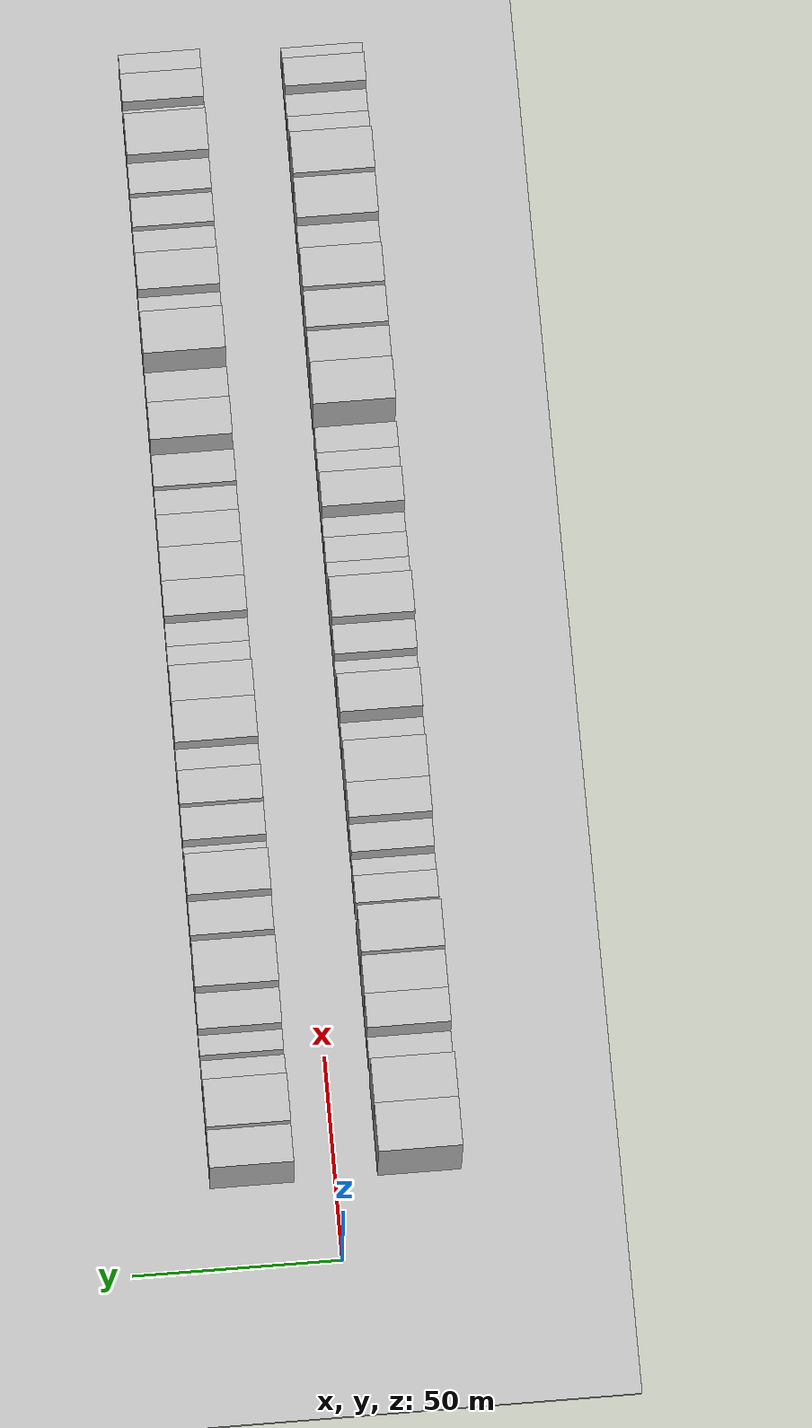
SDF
<?xml version="1.0" encoding="utf-8"?>

<sdf version="1.6">

   <world name="default">

      <gui fullscreen="0">

         <camera name="user_camera">

            <pose>-15 0 4.57585 0 0 0</pose>

            <view_controller>orbit</view_controller>

         </camera>

      </gui>

      <scene>

         <sky>

           <clouds>

             <speed>12</speed>

           </clouds>

         </sky>

         <ambient>0.4 0.4 0.4 1</ambient>

         <background>0.7 0.7 0.7 1</background>

         <shadows>1</shadows>

      </scene>

      <gravity>0 0 -9.8066</gravity>

      <magnetic_field>6e-06 2.3e-05 -4.2e-05</magnetic_field>

      <physics default="0" name="default_physics" type="ode">

         <ode>

            <solver>

               <type>quick</type>

               <iters>10</iters>

               <sor>1.0</sor>

               <use_dynamic_moi_rescaling>0</use_dynamic_moi_rescaling>

            </solver>

            <constraints>

               <cfm>0</cfm>

               <erp>0.2</erp>

               <contact_max_correcting_vel>100</contact_max_correcting_vel>

               <contact_surface_layer>0.001</contact_surface_layer>

            </constraints>

         </ode>

         <max_step_size>0.004</max_step_size>

         <real_time_factor>1</real_time_factor>

         <real_time_update_rate>250</real_time_update_rate>

      </physics>

      <light name="sun" type="directional">

         <cast_shadows>1</cast_shadows>

         <pose>0 0 10 0 0 0</pose>

         <diffuse>0.8 0.8 0.8 1</diffuse>

         <specular>0.2 0.2 0.2 1</specular>

         <attenuation>

            <range>1000</range>

            <constant>0.9</constant>

            <linear>0.01</linear>

            <quadratic>0.001</quadratic>

         </attenuation>

         <direction>-0.5 0.1 -0.9</direction>

      </light>

      <include>

         <name>ground_plane_1</name>

         <uri>model://HANNAS_ground_plane</uri>

         <pose>0 0 0  0 0 0</pose>

      </include>

      <include>

         <name>ground_plane_2</name>

         <uri>model://HANNAS_ground_plane</uri>

         <pose>100 0 0  0 0 0</pose>

      </include>

      <model name="building_1">

         <static>1</static>

         <pose frame="">24.6154 20.0000 0 0.000000 0.000000 1.570796</pose>

         <link name="link">

            <pose frame="">0 0 10.50 0 0 0</pose>

            <collision name="collision">

               <geometry>

                  <box>

                     <size>20.0000 9.2307 21.0000</size>

                  </box>

               </geometry>

               <max_contacts>10</max_contacts>

               <surface>

                  <contact>

                     <ode/>

                  </contact>

                  <bounce/>

                  <friction>

                     <torsional>

                        <ode/>

                     </torsional>

                     <ode/>

                  </friction>

               </surface>

            </collision>

            <visual name="visual">

               <cast_shadows>0</cast_shadows>

               <geometry>

                  <box>

                     <size>20.0000 9.2307 21.0000</size>

                  </box>

               </geometry>

               <material>

                  <script>

                     <uri>model://HANNAS_wall/materials/scripts</uri>

                     <uri>model://HANNAS_wall/materials/textures</uri>

                     <name>vrc/HANNAS_wall</name>

                  </script>

               </material>

            </visual>

            <self_collide>0</self_collide>

            <enable_wind>0</enable_wind>

            <kinematic>0</kinematic>

         </link>

      </model>

      <model name="building_2">

         <static>1</static>

         <pose frame="">35.0574 20.0000 0 0.000000 0.000000 1.570796</pose>

         <link name="link">

            <pose frame="">0 0 12.00 0 0 0</pose>

            <collision name="collision">

               <geometry>

                  <box>

                     <size>20.0000 11.6533 24.0000</size>

                  </box>

               </geometry>

               <max_contacts>10</max_contacts>

               <surface>

                  <contact>

                     <ode/>

                  </contact>

                  <bounce/>

                  <friction>

                     <torsional>

                        <ode/>

                     </torsional>

                     <ode/>

                  </friction>

               </surface>

            </collision>

            <visual name="visual">

               <cast_shadows>0</cast_shadows>

               <geometry>

                  <box>

                     <size>20.0000 11.6533 24.0000</size>

                  </box>

               </geometry>

               <material>

                  <script>

                     <uri>model://HANNAS_wall/materials/scripts</uri>

                     <uri>model://HANNAS_wall/materials/textures</uri>

                     <name>vrc/HANNAS_wall</name>

                  </script>

               </material>

            </visual>

            <self_collide>0</self_collide>

            <enable_wind>0</enable_wind>

            <kinematic>0</kinematic>

         </link>

      </model>

      <model name="building_3">

         <static>1</static>

         <pose frame="">44.3191 20.0000 0 0.000000 0.000000 1.570796</pose>

         <link name="link">

            <pose frame="">0 0 7.50 0 0 0</pose>

            <collision name="collision">

               <geometry>

                  <box>

                     <size>20.0000 6.8702 15.0000</size>

                  </box>

               </geometry>

               <max_contacts>10</max_contacts>

               <surface>

                  <contact>

                     <ode/>

                  </contact>

                  <bounce/>

                  <friction>

                     <torsional>

                        <ode/>

                     </torsional>

                     <ode/>

                  </friction>

               </surface>

            </collision>

            <visual name="visual">

               <cast_shadows>0</cast_shadows>

               <geometry>

                  <box>

                     <size>20.0000 6.8702 15.0000</size>

                  </box>

               </geometry>

               <material>

                  <script>

                     <uri>model://HANNAS_wall/materials/scripts</uri>

                     <uri>model://HANNAS_wall/materials/textures</uri>

                     <name>vrc/HANNAS_wall</name>

                  </script>

               </material>

            </visual>

            <self_collide>0</self_collide>

            <enable_wind>0</enable_wind>

            <kinematic>0</kinematic>

         </link>

      </model>

      <model name="building_4">

         <static>1</static>

         <pose frame="">52.2593 20.0000 0 0.000000 0.000000 1.570796</pose>

         <link name="link">

            <pose frame="">0 0 6.00 0 0 0</pose>

            <collision name="collision">

               <geometry>

                  <box>

                     <size>20.0000 5.0101 12.0000</size>

                  </box>

               </geometry>

               <max_contacts>10</max_contacts>

               <surface>

                  <contact>

                     <ode/>

                  </contact>

                  <bounce/>

                  <friction>

                     <torsional>

                        <ode/>

                     </torsional>

                     <ode/>

                  </friction>

               </surface>

            </collision>

            <visual name="visual">

               <cast_shadows>0</cast_shadows>

               <geometry>

                  <box>

                     <size>20.0000 5.0101 12.0000</size>

                  </box>

               </geometry>

               <material>

                  <script>

                     <uri>model://HANNAS_wall/materials/scripts</uri>

                     <uri>model://HANNAS_wall/materials/textures</uri>

                     <name>vrc/HANNAS_wall</name>

                  </script>

               </material>

            </visual>

            <self_collide>0</self_collide>

            <enable_wind>0</enable_wind>

            <kinematic>0</kinematic>

         </link>

      </model>

      <model name="building_5">

         <static>1</static>

         <pose frame="">59.1592 20.0000 0 0.000000 0.000000 1.570796</pose>

         <link name="link">

            <pose frame="">0 0 9.00 0 0 0</pose>

            <collision name="collision">

               <geometry>

                  <box>

                     <size>20.0000 8.7898 18.0000</size>

                  </box>

               </geometry>

               <max_contacts>10</max_contacts>

               <surface>

                  <contact>

                     <ode/>

                  </contact>

                  <bounce/>

                  <friction>

                     <torsional>

                        <ode/>

                     </torsional>

                     <ode/>

                  </friction>

               </surface>

            </collision>

            <visual name="visual">

               <cast_shadows>0</cast_shadows>

               <geometry>

                  <box>

                     <size>20.0000 8.7898 18.0000</size>

                  </box>

               </geometry>

               <material>

                  <script>

                     <uri>model://HANNAS_wall/materials/scripts</uri>

                     <uri>model://HANNAS_wall/materials/textures</uri>

                     <name>vrc/HANNAS_wall</name>

                  </script>

               </material>

            </visual>

            <self_collide>0</self_collide>

            <enable_wind>0</enable_wind>

            <kinematic>0</kinematic>

         </link>

      </model>

      <model name="building_6">

         <static>1</static>

         <pose frame="">69.2039 20.0000 0 0.000000 0.000000 1.570796</pose>

         <link name="link">

            <pose frame="">0 0 12.00 0 0 0</pose>

            <collision name="collision">

               <geometry>

                  <box>

                     <size>20.0000 11.2996 24.0000</size>

                  </box>

               </geometry>

               <max_contacts>10</max_contacts>

               <surface>

                  <contact>

                     <ode/>

                  </contact>

                  <bounce/>

                  <friction>

                     <torsional>

                        <ode/>

                     </torsional>

                     <ode/>

                  </friction>

               </surface>

            </collision>

            <visual name="visual">

               <cast_shadows>0</cast_shadows>

               <geometry>

                  <box>

                     <size>20.0000 11.2996 24.0000</size>

                  </box>

               </geometry>

               <material>

                  <script>

                     <uri>model://HANNAS_wall/materials/scripts</uri>

                     <uri>model://HANNAS_wall/materials/textures</uri>

                     <name>vrc/HANNAS_wall</name>

                  </script>

               </material>

            </visual>

            <self_collide>0</self_collide>

            <enable_wind>0</enable_wind>

            <kinematic>0</kinematic>

         </link>

      </model>

      <model name="building_7">

         <static>1</static>

         <pose frame="">82.0477 20.0000 0 0.000000 0.000000 1.570796</pose>

         <link name="link">

            <pose frame="">0 0 9.00 0 0 0</pose>

            <collision name="collision">

               <geometry>

                  <box>

                     <size>20.0000 8.3880 18.0000</size>

                  </box>

               </geometry>

               <max_contacts>10</max_contacts>

               <surface>

                  <contact>

                     <ode/>

                  </contact>

                  <bounce/>

                  <friction>

                     <torsional>

                        <ode/>

                     </torsional>

                     <ode/>

                  </friction>

               </surface>

            </collision>

            <visual name="visual">

               <cast_shadows>0</cast_shadows>

               <geometry>

                  <box>

                     <size>20.0000 8.3880 18.0000</size>

                  </box>

               </geometry>

               <material>

                  <script>

                     <uri>model://HANNAS_wall/materials/scripts</uri>

                     <uri>model://HANNAS_wall/materials/textures</uri>

                     <name>vrc/HANNAS_wall</name>

                  </script>

               </material>

            </visual>

            <self_collide>0</self_collide>

            <enable_wind>0</enable_wind>

            <kinematic>0</kinematic>

         </link>

      </model>

      <model name="building_8">

         <static>1</static>

         <pose frame="">91.3459 20.0000 0 0.000000 0.000000 1.570796</pose>

         <link name="link">

            <pose frame="">0 0 12.00 0 0 0</pose>

            <collision name="collision">

               <geometry>

                  <box>

                     <size>20.0000 10.2082 24.0000</size>

                  </box>

               </geometry>

               <max_contacts>10</max_contacts>

               <surface>

                  <contact>

                     <ode/>

                  </contact>

                  <bounce/>

                  <friction>

                     <torsional>

                        <ode/>

                     </torsional>

                     <ode/>

                  </friction>

               </surface>

            </collision>

            <visual name="visual">

               <cast_shadows>0</cast_shadows>

               <geometry>

                  <box>

                     <size>20.0000 10.2082 24.0000</size>

                  </box>

               </geometry>

               <material>

                  <script>

                     <uri>model://HANNAS_wall/materials/scripts</uri>

                     <uri>model://HANNAS_wall/materials/textures</uri>

                     <name>vrc/HANNAS_wall</name>

                  </script>

               </material>

            </visual>

            <self_collide>0</self_collide>

            <enable_wind>0</enable_wind>

            <kinematic>0</kinematic>

         </link>

      </model>

      <model name="building_9">

         <static>1</static>

         <pose frame="">98.9628 20.0000 0 0.000000 0.000000 1.570796</pose>

         <link name="link">

            <pose frame="">0 0 6.00 0 0 0</pose>

            <collision name="collision">

               <geometry>

                  <box>

                     <size>20.0000 5.0256 12.0000</size>

                  </box>

               </geometry>

               <max_contacts>10</max_contacts>

               <surface>

                  <contact>

                     <ode/>

                  </contact>

                  <bounce/>

                  <friction>

                     <torsional>

                        <ode/>

                     </torsional>

                     <ode/>

                  </friction>

               </surface>

            </collision>

            <visual name="visual">

               <cast_shadows>0</cast_shadows>

               <geometry>

                  <box>

                     <size>20.0000 5.0256 12.0000</size>

                  </box>

               </geometry>

               <material>

                  <script>

                     <uri>model://HANNAS_wall/materials/scripts</uri>

                     <uri>model://HANNAS_wall/materials/textures</uri>

                     <name>vrc/HANNAS_wall</name>

                  </script>

               </material>

            </visual>

            <self_collide>0</self_collide>

            <enable_wind>0</enable_wind>

            <kinematic>0</kinematic>

         </link>

      </model>

      <model name="building_10">

         <static>1</static>

         <pose frame="">105.5644 20.0000 0 0.000000 0.000000 1.570796</pose>

         <link name="link">

            <pose frame="">0 0 9.00 0 0 0</pose>

            <collision name="collision">

               <geometry>

                  <box>

                     <size>20.0000 8.1775 18.0000</size>

                  </box>

               </geometry>

               <max_contacts>10</max_contacts>

               <surface>

                  <contact>

                     <ode/>

                  </contact>

                  <bounce/>

                  <friction>

                     <torsional>

                        <ode/>

                     </torsional>

                     <ode/>

                  </friction>

               </surface>

            </collision>

            <visual name="visual">

               <cast_shadows>0</cast_shadows>

               <geometry>

                  <box>

                     <size>20.0000 8.1775 18.0000</size>

                  </box>

               </geometry>

               <material>

                  <script>

                     <uri>model://HANNAS_wall/materials/scripts</uri>

                     <uri>model://HANNAS_wall/materials/textures</uri>

                     <name>vrc/HANNAS_wall</name>

                  </script>

               </material>

            </visual>

            <self_collide>0</self_collide>

            <enable_wind>0</enable_wind>

            <kinematic>0</kinematic>

         </link>

      </model>

      <model name="building_11">

         <static>1</static>

         <pose frame="">113.8745 20.0000 0 0.000000 0.000000 1.570796</pose>

         <link name="link">

            <pose frame="">0 0 10.50 0 0 0</pose>

            <collision name="collision">

               <geometry>

                  <box>

                     <size>20.0000 8.4427 21.0000</size>

                  </box>

               </geometry>

               <max_contacts>10</max_contacts>

               <surface>

                  <contact>

                     <ode/>

                  </contact>

                  <bounce/>

                  <friction>

                     <torsional>

                        <ode/>

                     </torsional>

                     <ode/>

                  </friction>

               </surface>

            </collision>

            <visual name="visual">

               <cast_shadows>0</cast_shadows>

               <geometry>

                  <box>

                     <size>20.0000 8.4427 21.0000</size>

                  </box>

               </geometry>

               <material>

                  <script>

                     <uri>model://HANNAS_wall/materials/scripts</uri>

                     <uri>model://HANNAS_wall/materials/textures</uri>

                     <name>vrc/HANNAS_wall</name>

                  </script>

               </material>

            </visual>

            <self_collide>0</self_collide>

            <enable_wind>0</enable_wind>

            <kinematic>0</kinematic>

         </link>

      </model>

      <model name="building_12">

         <static>1</static>

         <pose frame="">121.5920 20.0000 0 0.000000 0.000000 1.570796</pose>

         <link name="link">

            <pose frame="">0 0 7.50 0 0 0</pose>

            <collision name="collision">

               <geometry>

                  <box>

                     <size>20.0000 6.9923 15.0000</size>

                  </box>

               </geometry>

               <max_contacts>10</max_contacts>

               <surface>

                  <contact>

                     <ode/>

                  </contact>

                  <bounce/>

                  <friction>

                     <torsional>

                        <ode/>

                     </torsional>

                     <ode/>

                  </friction>

               </surface>

            </collision>

            <visual name="visual">

               <cast_shadows>0</cast_shadows>

               <geometry>

                  <box>

                     <size>20.0000 6.9923 15.0000</size>

                  </box>

               </geometry>

               <material>

                  <script>

                     <uri>model://HANNAS_wall/materials/scripts</uri>

                     <uri>model://HANNAS_wall/materials/textures</uri>

                     <name>vrc/HANNAS_wall</name>

                  </script>

               </material>

            </visual>

            <self_collide>0</self_collide>

            <enable_wind>0</enable_wind>

            <kinematic>0</kinematic>

         </link>

      </model>

      <model name="building_13">

         <static>1</static>

         <pose frame="">130.2661 20.0000 0 0.000000 0.000000 1.570796</pose>

         <link name="link">

            <pose frame="">0 0 10.50 0 0 0</pose>

            <collision name="collision">

               <geometry>

                  <box>

                     <size>20.0000 10.3558 21.0000</size>

                  </box>

               </geometry>

               <max_contacts>10</max_contacts>

               <surface>

                  <contact>

                     <ode/>

                  </contact>

                  <bounce/>

                  <friction>

                     <torsional>

                        <ode/>

                     </torsional>

                     <ode/>

                  </friction>

               </surface>

            </collision>

            <visual name="visual">

               <cast_shadows>0</cast_shadows>

               <geometry>

                  <box>

                     <size>20.0000 10.3558 21.0000</size>

                  </box>

               </geometry>

               <material>

                  <script>

                     <uri>model://HANNAS_wall/materials/scripts</uri>

                     <uri>model://HANNAS_wall/materials/textures</uri>

                     <name>vrc/HANNAS_wall</name>

                  </script>

               </material>

            </visual>

            <self_collide>0</self_collide>

            <enable_wind>0</enable_wind>

            <kinematic>0</kinematic>

         </link>

      </model>

      <model name="building_14">

         <static>1</static>

         <pose frame="">139.9339 20.0000 0 0.000000 0.000000 1.570796</pose>

         <link name="link">

            <pose frame="">0 0 10.50 0 0 0</pose>

            <collision name="collision">

               <geometry>

                  <box>

                     <size>20.0000 8.9798 21.0000</size>

                  </box>

               </geometry>

               <max_contacts>10</max_contacts>

               <surface>

                  <contact>

                     <ode/>

                  </contact>

                  <bounce/>

                  <friction>

                     <torsional>

                        <ode/>

                     </torsional>

                     <ode/>

                  </friction>

               </surface>

            </collision>

            <visual name="visual">

               <cast_shadows>0</cast_shadows>

               <geometry>

                  <box>

                     <size>20.0000 8.9798 21.0000</size>

                  </box>

               </geometry>

               <material>

                  <script>

                     <uri>model://HANNAS_wall/materials/scripts</uri>

                     <uri>model://HANNAS_wall/materials/textures</uri>

                     <name>vrc/HANNAS_wall</name>

                  </script>

               </material>

            </visual>

            <self_collide>0</self_collide>

            <enable_wind>0</enable_wind>

            <kinematic>0</kinematic>

         </link>

      </model>

      <model name="building_15">

         <static>1</static>

         <pose frame="">149.1682 20.0000 0 0.000000 0.000000 1.570796</pose>

         <link name="link">

            <pose frame="">0 0 6.00 0 0 0</pose>

            <collision name="collision">

               <geometry>

                  <box>

                     <size>20.0000 5.4888 12.0000</size>

                  </box>

               </geometry>

               <max_contacts>10</max_contacts>

               <surface>

                  <contact>

                     <ode/>

                  </contact>

                  <bounce/>

                  <friction>

                     <torsional>

                        <ode/>

                     </torsional>

                     <ode/>

                  </friction>

               </surface>

            </collision>

            <visual name="visual">

               <cast_shadows>0</cast_shadows>

               <geometry>

                  <box>

                     <size>20.0000 5.4888 12.0000</size>

                  </box>

               </geometry>

               <material>

                  <script>

                     <uri>model://HANNAS_wall/materials/scripts</uri>

                     <uri>model://HANNAS_wall/materials/textures</uri>

                     <name>vrc/HANNAS_wall</name>

                  </script>

               </material>

            </visual>

            <self_collide>0</self_collide>

            <enable_wind>0</enable_wind>

            <kinematic>0</kinematic>

         </link>

      </model>

      <model name="building_16">

         <static>1</static>

         <pose frame="">154.8276 20.0000 0 0.000000 0.000000 1.570796</pose>

         <link name="link">

            <pose frame="">0 0 6.00 0 0 0</pose>

            <collision name="collision">

               <geometry>

                  <box>

                     <size>20.0000 5.8300 12.0000</size>

                  </box>

               </geometry>

               <max_contacts>10</max_contacts>

               <surface>

                  <contact>

                     <ode/>

                  </contact>

                  <bounce/>

                  <friction>

                     <torsional>

                        <ode/>

                     </torsional>

                     <ode/>

                  </friction>

               </surface>

            </collision>

            <visual name="visual">

               <cast_shadows>0</cast_shadows>

               <geometry>

                  <box>

                     <size>20.0000 5.8300 12.0000</size>

                  </box>

               </geometry>

               <material>

                  <script>

                     <uri>model://HANNAS_wall/materials/scripts</uri>

                     <uri>model://HANNAS_wall/materials/textures</uri>

                     <name>vrc/HANNAS_wall</name>

                  </script>

               </material>

            </visual>

            <self_collide>0</self_collide>

            <enable_wind>0</enable_wind>

            <kinematic>0</kinematic>

         </link>

      </model>

      <model name="building_17">

         <static>1</static>

         <pose frame="">162.2196 20.0000 0 0.000000 0.000000 1.570796</pose>

         <link name="link">

            <pose frame="">0 0 9.00 0 0 0</pose>

            <collision name="collision">

               <geometry>

                  <box>

                     <size>20.0000 8.9540 18.0000</size>

                  </box>

               </geometry>

               <max_contacts>10</max_contacts>

               <surface>

                  <contact>

                     <ode/>

                  </contact>

                  <bounce/>

                  <friction>

                     <torsional>

                        <ode/>

                     </torsional>

                     <ode/>

                  </friction>

               </surface>

            </collision>

            <visual name="visual">

               <cast_shadows>0</cast_shadows>

               <geometry>

                  <box>

                     <size>20.0000 8.9540 18.0000</size>

                  </box>

               </geometry>

               <material>

                  <script>

                     <uri>model://HANNAS_wall/materials/scripts</uri>

                     <uri>model://HANNAS_wall/materials/textures</uri>

                     <name>vrc/HANNAS_wall</name>

                  </script>

               </material>

            </visual>

            <self_collide>0</self_collide>

            <enable_wind>0</enable_wind>

            <kinematic>0</kinematic>

         </link>

      </model>

      <model name="building_18">

         <static>1</static>

         <pose frame="">170.9655 20.0000 0 0.000000 0.000000 1.570796</pose>

         <link name="link">

            <pose frame="">0 0 9.00 0 0 0</pose>

            <collision name="collision">

               <geometry>

                  <box>

                     <size>20.0000 8.5378 18.0000</size>

                  </box>

               </geometry>

               <max_contacts>10</max_contacts>

               <surface>

                  <contact>

                     <ode/>

                  </contact>

                  <bounce/>

                  <friction>

                     <torsional>

                        <ode/>

                     </torsional>

                     <ode/>

                  </friction>

               </surface>

            </collision>

            <visual name="visual">

               <cast_shadows>0</cast_shadows>

               <geometry>

                  <box>

                     <size>20.0000 8.5378 18.0000</size>

                  </box>

               </geometry>

               <material>

                  <script>

                     <uri>model://HANNAS_wall/materials/scripts</uri>

                     <uri>model://HANNAS_wall/materials/textures</uri>

                     <name>vrc/HANNAS_wall</name>

                  </script>

               </material>

            </visual>

            <self_collide>0</self_collide>

            <enable_wind>0</enable_wind>

            <kinematic>0</kinematic>

         </link>

      </model>

      <model name="building_19">

         <static>1</static>

         <pose frame="">179.3129 20.0000 0 0.000000 0.000000 1.570796</pose>

         <link name="link">

            <pose frame="">0 0 9.00 0 0 0</pose>

            <collision name="collision">

               <geometry>

                  <box>

                     <size>20.0000 8.1570 18.0000</size>

                  </box>

               </geometry>

               <max_contacts>10</max_contacts>

               <surface>

                  <contact>

                     <ode/>

                  </contact>

                  <bounce/>

                  <friction>

                     <torsional>

                        <ode/>

                     </torsional>

                     <ode/>

                  </friction>

               </surface>

            </collision>

            <visual name="visual">

               <cast_shadows>0</cast_shadows>

               <geometry>

                  <box>

                     <size>20.0000 8.1570 18.0000</size>

                  </box>

               </geometry>

               <material>

                  <script>

                     <uri>model://HANNAS_wall/materials/scripts</uri>

                     <uri>model://HANNAS_wall/materials/textures</uri>

                     <name>vrc/HANNAS_wall</name>

                  </script>

               </material>

            </visual>

            <self_collide>0</self_collide>

            <enable_wind>0</enable_wind>

            <kinematic>0</kinematic>

         </link>

      </model>

      <model name="building_20">

         <static>1</static>

         <pose frame="">186.9675 20.0000 0 0.000000 0.000000 1.570796</pose>

         <link name="link">

            <pose frame="">0 0 7.50 0 0 0</pose>

            <collision name="collision">

               <geometry>

                  <box>

                     <size>20.0000 7.1522 15.0000</size>

                  </box>

               </geometry>

               <max_contacts>10</max_contacts>

               <surface>

                  <contact>

                     <ode/>

                  </contact>

                  <bounce/>

                  <friction>

                     <torsional>

                        <ode/>

                     </torsional>

                     <ode/>

                  </friction>

               </surface>

            </collision>

            <visual name="visual">

               <cast_shadows>0</cast_shadows>

               <geometry>

                  <box>

                     <size>20.0000 7.1522 15.0000</size>

                  </box>

               </geometry>

               <material>

                  <script>

                     <uri>model://HANNAS_wall/materials/scripts</uri>

                     <uri>model://HANNAS_wall/materials/textures</uri>

                     <name>vrc/HANNAS_wall</name>

                  </script>

               </material>

            </visual>

            <self_collide>0</self_collide>

            <enable_wind>0</enable_wind>

            <kinematic>0</kinematic>

         </link>

      </model>

      <model name="building_21">

         <static>1</static>

         <pose frame="">194.6178 20.0000 0 0.000000 0.000000 1.570796</pose>

         <link name="link">

            <pose frame="">0 0 9.00 0 0 0</pose>

            <collision name="collision">

               <geometry>

                  <box>

                     <size>20.0000 8.1486 18.0000</size>

                  </box>

               </geometry>

               <max_contacts>10</max_contacts>

               <surface>

                  <contact>

                     <ode/>

                  </contact>

                  <bounce/>

                  <friction>

                     <torsional>

                        <ode/>

                     </torsional>

                     <ode/>

                  </friction>

               </surface>

            </collision>

            <visual name="visual">

               <cast_shadows>0</cast_shadows>

               <geometry>

                  <box>

                     <size>20.0000 8.1486 18.0000</size>

                  </box>

               </geometry>

               <material>

                  <script>

                     <uri>model://HANNAS_wall/materials/scripts</uri>

                     <uri>model://HANNAS_wall/materials/textures</uri>

                     <name>vrc/HANNAS_wall</name>

                  </script>

               </material>

            </visual>

            <self_collide>0</self_collide>

            <enable_wind>0</enable_wind>

            <kinematic>0</kinematic>

         </link>

      </model>

      <model name="building_22">

         <static>1</static>

         <pose frame="">206.4582 20.0000 0 0.000000 0.000000 1.570796</pose>

         <link name="link">

            <pose frame="">0 0 10.50 0 0 0</pose>

            <collision name="collision">

               <geometry>

                  <box>

                     <size>20.0000 9.5322 21.0000</size>

                  </box>

               </geometry>

               <max_contacts>10</max_contacts>

               <surface>

                  <contact>

                     <ode/>

                  </contact>

                  <bounce/>

                  <friction>

                     <torsional>

                        <ode/>

                     </torsional>

                     <ode/>

                  </friction>

               </surface>

            </collision>

            <visual name="visual">

               <cast_shadows>0</cast_shadows>

               <geometry>

                  <box>

                     <size>20.0000 9.5322 21.0000</size>

                  </box>

               </geometry>

               <material>

                  <script>

                     <uri>model://HANNAS_wall/materials/scripts</uri>

                     <uri>model://HANNAS_wall/materials/textures</uri>

                     <name>vrc/HANNAS_wall</name>

                  </script>

               </material>

            </visual>

            <self_collide>0</self_collide>

            <enable_wind>0</enable_wind>

            <kinematic>0</kinematic>

         </link>

      </model>

      <model name="building_23">

         <static>1</static>

         <pose frame="">215.4928 20.0000 0 0.000000 0.000000 1.570796</pose>

         <link name="link">

            <pose frame="">0 0 9.00 0 0 0</pose>

            <collision name="collision">

               <geometry>

                  <box>

                     <size>20.0000 8.5369 18.0000</size>

                  </box>

               </geometry>

               <max_contacts>10</max_contacts>

               <surface>

                  <contact>

                     <ode/>

                  </contact>

                  <bounce/>

                  <friction>

                     <torsional>

                        <ode/>

                     </torsional>

                     <ode/>

                  </friction>

               </surface>

            </collision>

            <visual name="visual">

               <cast_shadows>0</cast_shadows>

               <geometry>

                  <box>

                     <size>20.0000 8.5369 18.0000</size>

                  </box>

               </geometry>

               <material>

                  <script>

                     <uri>model://HANNAS_wall/materials/scripts</uri>

                     <uri>model://HANNAS_wall/materials/textures</uri>

                     <name>vrc/HANNAS_wall</name>

                  </script>

               </material>

            </visual>

            <self_collide>0</self_collide>

            <enable_wind>0</enable_wind>

            <kinematic>0</kinematic>

         </link>

      </model>

      <model name="building_24">

         <static>1</static>

         <pose frame="">228.1328 20.0000 0 0.000000 0.000000 1.570796</pose>

         <link name="link">

            <pose frame="">0 0 12.00 0 0 0</pose>

            <collision name="collision">

               <geometry>

                  <box>

                     <size>20.0000 10.7432 24.0000</size>

                  </box>

               </geometry>

               <max_contacts>10</max_contacts>

               <surface>

                  <contact>

                     <ode/>

                  </contact>

                  <bounce/>

                  <friction>

                     <torsional>

                        <ode/>

                     </torsional>

                     <ode/>

                  </friction>

               </surface>

            </collision>

            <visual name="visual">

               <cast_shadows>0</cast_shadows>

               <geometry>

                  <box>

                     <size>20.0000 10.7432 24.0000</size>

                  </box>

               </geometry>

               <material>

                  <script>

                     <uri>model://HANNAS_wall/materials/scripts</uri>

                     <uri>model://HANNAS_wall/materials/textures</uri>

                     <name>vrc/HANNAS_wall</name>

                  </script>

               </material>

            </visual>

            <self_collide>0</self_collide>

            <enable_wind>0</enable_wind>

            <kinematic>0</kinematic>

         </link>

      </model>

      <model name="building_25">

         <static>1</static>

         <pose frame="">236.8446 20.0000 0 0.000000 0.000000 1.570796</pose>

         <link name="link">

            <pose frame="">0 0 7.50 0 0 0</pose>

            <collision name="collision">

               <geometry>

                  <box>

                     <size>20.0000 6.6804 15.0000</size>

                  </box>

               </geometry>

               <max_contacts>10</max_contacts>

               <surface>

                  <contact>

                     <ode/>

                  </contact>

                  <bounce/>

                  <friction>

                     <torsional>

                        <ode/>

                     </torsional>

                     <ode/>

                  </friction>

               </surface>

            </collision>

            <visual name="visual">

               <cast_shadows>0</cast_shadows>

               <geometry>

                  <box>

                     <size>20.0000 6.6804 15.0000</size>

                  </box>

               </geometry>

               <material>

                  <script>

                     <uri>model://HANNAS_wall/materials/scripts</uri>

                     <uri>model://HANNAS_wall/materials/textures</uri>

                     <name>vrc/HANNAS_wall</name>

                  </script>

               </material>

            </visual>

            <self_collide>0</self_collide>

            <enable_wind>0</enable_wind>

            <kinematic>0</kinematic>

         </link>

      </model>

      <model name="building_26">

         <static>1</static>

         <pose frame="">244.9300 20.0000 0 0.000000 0.000000 1.570796</pose>

         <link name="link">

            <pose frame="">0 0 10.50 0 0 0</pose>

            <collision name="collision">

               <geometry>

                  <box>

                     <size>20.0000 9.4905 21.0000</size>

                  </box>

               </geometry>

               <max_contacts>10</max_contacts>

               <surface>

                  <contact>

                     <ode/>

                  </contact>

                  <bounce/>

                  <friction>

                     <torsional>

                        <ode/>

                     </torsional>

                     <ode/>

                  </friction>

               </surface>

            </collision>

            <visual name="visual">

               <cast_shadows>0</cast_shadows>

               <geometry>

                  <box>

                     <size>20.0000 9.4905 21.0000</size>

                  </box>

               </geometry>

               <material>

                  <script>

                     <uri>model://HANNAS_wall/materials/scripts</uri>

                     <uri>model://HANNAS_wall/materials/textures</uri>

                     <name>vrc/HANNAS_wall</name>

                  </script>

               </material>

            </visual>

            <self_collide>0</self_collide>

            <enable_wind>0</enable_wind>

            <kinematic>0</kinematic>

         </link>

      </model>

      <model name="building_27">

         <static>1</static>

         <pose frame="">254.0313 20.0000 0 0.000000 0.000000 1.570796</pose>

         <link name="link">

            <pose frame="">0 0 7.50 0 0 0</pose>

            <collision name="collision">

               <geometry>

                  <box>

                     <size>20.0000 6.7121 15.0000</size>

                  </box>

               </geometry>

               <max_contacts>10</max_contacts>

               <surface>

                  <contact>

                     <ode/>

                  </contact>

                  <bounce/>

                  <friction>

                     <torsional>

                        <ode/>

                     </torsional>

                     <ode/>

                  </friction>

               </surface>

            </collision>

            <visual name="visual">

               <cast_shadows>0</cast_shadows>

               <geometry>

                  <box>

                     <size>20.0000 6.7121 15.0000</size>

                  </box>

               </geometry>

               <material>

                  <script>

                     <uri>model://HANNAS_wall/materials/scripts</uri>

                     <uri>model://HANNAS_wall/materials/textures</uri>

                     <name>vrc/HANNAS_wall</name>

                  </script>

               </material>

            </visual>

            <self_collide>0</self_collide>

            <enable_wind>0</enable_wind>

            <kinematic>0</kinematic>

         </link>

      </model>

      <model name="building_28">

         <static>1</static>

         <pose frame="">261.1885 20.0000 0 0.000000 0.000000 1.570796</pose>

         <link name="link">

            <pose frame="">0 0 9.00 0 0 0</pose>

            <collision name="collision">

               <geometry>

                  <box>

                     <size>20.0000 7.6023 18.0000</size>

                  </box>

               </geometry>

               <max_contacts>10</max_contacts>

               <surface>

                  <contact>

                     <ode/>

                  </contact>

                  <bounce/>

                  <friction>

                     <torsional>

                        <ode/>

                     </torsional>

                     <ode/>

                  </friction>

               </surface>

            </collision>

            <visual name="visual">

               <cast_shadows>0</cast_shadows>

               <geometry>

                  <box>

                     <size>20.0000 7.6023 18.0000</size>

                  </box>

               </geometry>

               <material>

                  <script>

                     <uri>model://HANNAS_wall/materials/scripts</uri>

                     <uri>model://HANNAS_wall/materials/textures</uri>

                     <name>vrc/HANNAS_wall</name>

                  </script>

               </material>

            </visual>

            <self_collide>0</self_collide>

            <enable_wind>0</enable_wind>

            <kinematic>0</kinematic>

         </link>

      </model>

      <model name="building_29">

         <static>1</static>

         <pose frame="">269.9641 20.0000 0 0.000000 0.000000 1.570796</pose>

         <link name="link">

            <pose frame="">0 0 9.00 0 0 0</pose>

            <collision name="collision">

               <geometry>

                  <box>

                     <size>20.0000 7.9489 18.0000</size>

                  </box>

               </geometry>

               <max_contacts>10</max_contacts>

               <surface>

                  <contact>

                     <ode/>

                  </contact>

                  <bounce/>

                  <friction>

                     <torsional>

                        <ode/>

                     </torsional>

                     <ode/>

                  </friction>

               </surface>

            </collision>

            <visual name="visual">

               <cast_shadows>0</cast_shadows>

               <geometry>

                  <box>

                     <size>20.0000 7.9489 18.0000</size>

                  </box>

               </geometry>

               <material>

                  <script>

                     <uri>model://HANNAS_wall/materials/scripts</uri>

                     <uri>model://HANNAS_wall/materials/textures</uri>

                     <name>vrc/HANNAS_wall</name>

                  </script>

               </material>

            </visual>

            <self_collide>0</self_collide>

            <enable_wind>0</enable_wind>

            <kinematic>0</kinematic>

         </link>

      </model>

      <model name="building_30">

         <static>1</static>

         <pose frame="">279.3393 20.0000 0 0.000000 0.000000 1.570796</pose>

         <link name="link">

            <pose frame="">0 0 12.00 0 0 0</pose>

            <collision name="collision">

               <geometry>

                  <box>

                     <size>20.0000 10.8015 24.0000</size>

                  </box>

               </geometry>

               <max_contacts>10</max_contacts>

               <surface>

                  <contact>

                     <ode/>

                  </contact>

                  <bounce/>

                  <friction>

                     <torsional>

                        <ode/>

                     </torsional>

                     <ode/>

                  </friction>

               </surface>

            </collision>

            <visual name="visual">

               <cast_shadows>0</cast_shadows>

               <geometry>

                  <box>

                     <size>20.0000 10.8015 24.0000</size>

                  </box>

               </geometry>

               <material>

                  <script>

                     <uri>model://HANNAS_wall/materials/scripts</uri>

                     <uri>model://HANNAS_wall/materials/textures</uri>

                     <name>vrc/HANNAS_wall</name>

                  </script>

               </material>

            </visual>

            <self_collide>0</self_collide>

            <enable_wind>0</enable_wind>

            <kinematic>0</kinematic>

         </link>

      </model>

      <model name="building_31">

         <static>1</static>

         <pose frame="">287.3573 20.0000 0 0.000000 0.000000 1.570796</pose>

         <link name="link">

            <pose frame="">0 0 6.00 0 0 0</pose>

            <collision name="collision">

               <geometry>

                  <box>

                     <size>20.0000 5.2344 12.0000</size>

                  </box>

               </geometry>

               <max_contacts>10</max_contacts>

               <surface>

                  <contact>

                     <ode/>

                  </contact>

                  <bounce/>

                  <friction>

                     <torsional>

                        <ode/>

                     </torsional>

                     <ode/>

                  </friction>

               </surface>

            </collision>

            <visual name="visual">

               <cast_shadows>0</cast_shadows>

               <geometry>

                  <box>

                     <size>20.0000 5.2344 12.0000</size>

                  </box>

               </geometry>

               <material>

                  <script>

                     <uri>model://HANNAS_wall/materials/scripts</uri>

                     <uri>model://HANNAS_wall/materials/textures</uri>

                     <name>vrc/HANNAS_wall</name>

                  </script>

               </material>

            </visual>

            <self_collide>0</self_collide>

            <enable_wind>0</enable_wind>

            <kinematic>0</kinematic>

         </link>

      </model>

      <model name="building_32">

         <static>1</static>

         <pose frame="">293.6789 20.0000 0 0.000000 0.000000 1.570796</pose>

         <link name="link">

            <pose frame="">0 0 9.00 0 0 0</pose>

            <collision name="collision">

               <geometry>

                  <box>

                     <size>20.0000 7.4087 18.0000</size>

                  </box>

               </geometry>

               <max_contacts>10</max_contacts>

               <surface>

                  <contact>

                     <ode/>

                  </contact>

                  <bounce/>

                  <friction>

                     <torsional>

                        <ode/>

                     </torsional>

                     <ode/>

                  </friction>

               </surface>

            </collision>

            <visual name="visual">

               <cast_shadows>0</cast_shadows>

               <geometry>

                  <box>

                     <size>20.0000 7.4087 18.0000</size>

                  </box>

               </geometry>

               <material>

                  <script>

                     <uri>model://HANNAS_wall/materials/scripts</uri>

                     <uri>model://HANNAS_wall/materials/textures</uri>

                     <name>vrc/HANNAS_wall</name>

                  </script>

               </material>

            </visual>

            <self_collide>0</self_collide>

            <enable_wind>0</enable_wind>

            <kinematic>0</kinematic>

         </link>

      </model>

      <model name="building_33">

         <static>1</static>

         <pose frame="">300.4139 20.0000 0 0.000000 0.000000 1.570796</pose>

         <link name="link">

            <pose frame="">0 0 7.50 0 0 0</pose>

            <collision name="collision">

               <geometry>

                  <box>

                     <size>20.0000 6.0613 15.0000</size>

                  </box>

               </geometry>

               <max_contacts>10</max_contacts>

               <surface>

                  <contact>

                     <ode/>

                  </contact>

                  <bounce/>

                  <friction>

                     <torsional>

                        <ode/>

                     </torsional>

                     <ode/>

                  </friction>

               </surface>

            </collision>

            <visual name="visual">

               <cast_shadows>0</cast_shadows>

               <geometry>

                  <box>

                     <size>20.0000 6.0613 15.0000</size>

                  </box>

               </geometry>

               <material>

                  <script>

                     <uri>model://HANNAS_wall/materials/scripts</uri>

                     <uri>model://HANNAS_wall/materials/textures</uri>

                     <name>vrc/HANNAS_wall</name>

                  </script>

               </material>

            </visual>

            <self_collide>0</self_collide>

            <enable_wind>0</enable_wind>

            <kinematic>0</kinematic>

         </link>

      </model>

      <model name="building_34">

         <static>1</static>

         <pose frame="">25.9539 -20.0000 0 0.000000 0.000000 1.570796</pose>

         <link name="link">

            <pose frame="">0 0 12.00 0 0 0</pose>

            <collision name="collision">

               <geometry>

                  <box>

                     <size>20.0000 11.9078 24.0000</size>

                  </box>

               </geometry>

               <max_contacts>10</max_contacts>

               <surface>

                  <contact>

                     <ode/>

                  </contact>

                  <bounce/>

                  <friction>

                     <torsional>

                        <ode/>

                     </torsional>

                     <ode/>

                  </friction>

               </surface>

            </collision>

            <visual name="visual">

               <cast_shadows>0</cast_shadows>

               <geometry>

                  <box>

                     <size>20.0000 11.9078 24.0000</size>

                  </box>

               </geometry>

               <material>

                  <script>

                     <uri>model://HANNAS_wall/materials/scripts</uri>

                     <uri>model://HANNAS_wall/materials/textures</uri>

                     <name>vrc/HANNAS_wall</name>

                  </script>

               </material>

            </visual>

            <self_collide>0</self_collide>

            <enable_wind>0</enable_wind>

            <kinematic>0</kinematic>

         </link>

      </model>

      <model name="building_35">

         <static>1</static>

         <pose frame="">37.3407 -20.0000 0 0.000000 0.000000 1.570796</pose>

         <link name="link">

            <pose frame="">0 0 12.00 0 0 0</pose>

            <collision name="collision">

               <geometry>

                  <box>

                     <size>20.0000 10.8658 24.0000</size>

                  </box>

               </geometry>

               <max_contacts>10</max_contacts>

               <surface>

                  <contact>

                     <ode/>

                  </contact>

                  <bounce/>

                  <friction>

                     <torsional>

                        <ode/>

                     </torsional>

                     <ode/>

                  </friction>

               </surface>

            </collision>

            <visual name="visual">

               <cast_shadows>0</cast_shadows>

               <geometry>

                  <box>

                     <size>20.0000 10.8658 24.0000</size>

                  </box>

               </geometry>

               <material>

                  <script>

                     <uri>model://HANNAS_wall/materials/scripts</uri>

                     <uri>model://HANNAS_wall/materials/textures</uri>

                     <name>vrc/HANNAS_wall</name>

                  </script>

               </material>

            </visual>

            <self_collide>0</self_collide>

            <enable_wind>0</enable_wind>

            <kinematic>0</kinematic>

         </link>

      </model>

      <model name="building_36">

         <static>1</static>

         <pose frame="">48.4187 -20.0000 0 0.000000 0.000000 1.570796</pose>

         <link name="link">

            <pose frame="">0 0 6.00 0 0 0</pose>

            <collision name="collision">

               <geometry>

                  <box>

                     <size>20.0000 5.2903 12.0000</size>

                  </box>

               </geometry>

               <max_contacts>10</max_contacts>

               <surface>

                  <contact>

                     <ode/>

                  </contact>

                  <bounce/>

                  <friction>

                     <torsional>

                        <ode/>

                     </torsional>

                     <ode/>

                  </friction>

               </surface>

            </collision>

            <visual name="visual">

               <cast_shadows>0</cast_shadows>

               <geometry>

                  <box>

                     <size>20.0000 5.2903 12.0000</size>

                  </box>

               </geometry>

               <material>

                  <script>

                     <uri>model://HANNAS_wall/materials/scripts</uri>

                     <uri>model://HANNAS_wall/materials/textures</uri>

                     <name>vrc/HANNAS_wall</name>

                  </script>

               </material>

            </visual>

            <self_collide>0</self_collide>

            <enable_wind>0</enable_wind>

            <kinematic>0</kinematic>

         </link>

      </model>

      <model name="building_37">

         <static>1</static>

         <pose frame="">55.2820 -20.0000 0 0.000000 0.000000 1.570796</pose>

         <link name="link">

            <pose frame="">0 0 10.50 0 0 0</pose>

            <collision name="collision">

               <geometry>

                  <box>

                     <size>20.0000 8.4362 21.0000</size>

                  </box>

               </geometry>

               <max_contacts>10</max_contacts>

               <surface>

                  <contact>

                     <ode/>

                  </contact>

                  <bounce/>

                  <friction>

                     <torsional>

                        <ode/>

                     </torsional>

                     <ode/>

                  </friction>

               </surface>

            </collision>

            <visual name="visual">

               <cast_shadows>0</cast_shadows>

               <geometry>

                  <box>

                     <size>20.0000 8.4362 21.0000</size>

                  </box>

               </geometry>

               <material>

                  <script>

                     <uri>model://HANNAS_wall/materials/scripts</uri>

                     <uri>model://HANNAS_wall/materials/textures</uri>

                     <name>vrc/HANNAS_wall</name>

                  </script>

               </material>

            </visual>

            <self_collide>0</self_collide>

            <enable_wind>0</enable_wind>

            <kinematic>0</kinematic>

         </link>

      </model>

      <model name="building_38">

         <static>1</static>

         <pose frame="">64.2011 -20.0000 0 0.000000 0.000000 1.570796</pose>

         <link name="link">

            <pose frame="">0 0 10.50 0 0 0</pose>

            <collision name="collision">

               <geometry>

                  <box>

                     <size>20.0000 9.4021 21.0000</size>

                  </box>

               </geometry>

               <max_contacts>10</max_contacts>

               <surface>

                  <contact>

                     <ode/>

                  </contact>

                  <bounce/>

                  <friction>

                     <torsional>

                        <ode/>

                     </torsional>

                     <ode/>

                  </friction>

               </surface>

            </collision>

            <visual name="visual">

               <cast_shadows>0</cast_shadows>

               <geometry>

                  <box>

                     <size>20.0000 9.4021 21.0000</size>

                  </box>

               </geometry>

               <material>

                  <script>

                     <uri>model://HANNAS_wall/materials/scripts</uri>

                     <uri>model://HANNAS_wall/materials/textures</uri>

                     <name>vrc/HANNAS_wall</name>

                  </script>

               </material>

            </visual>

            <self_collide>0</self_collide>

            <enable_wind>0</enable_wind>

            <kinematic>0</kinematic>

         </link>

      </model>

      <model name="building_39">

         <static>1</static>

         <pose frame="">74.7016 -20.0000 0 0.000000 0.000000 1.570796</pose>

         <link name="link">

            <pose frame="">0 0 12.00 0 0 0</pose>

            <collision name="collision">

               <geometry>

                  <box>

                     <size>20.0000 11.5989 24.0000</size>

                  </box>

               </geometry>

               <max_contacts>10</max_contacts>

               <surface>

                  <contact>

                     <ode/>

                  </contact>

                  <bounce/>

                  <friction>

                     <torsional>

                        <ode/>

                     </torsional>

                     <ode/>

                  </friction>

               </surface>

            </collision>

            <visual name="visual">

               <cast_shadows>0</cast_shadows>

               <geometry>

                  <box>

                     <size>20.0000 11.5989 24.0000</size>

                  </box>

               </geometry>

               <material>

                  <script>

                     <uri>model://HANNAS_wall/materials/scripts</uri>

                     <uri>model://HANNAS_wall/materials/textures</uri>

                     <name>vrc/HANNAS_wall</name>

                  </script>

               </material>

            </visual>

            <self_collide>0</self_collide>

            <enable_wind>0</enable_wind>

            <kinematic>0</kinematic>

         </link>

      </model>

      <model name="building_40">

         <static>1</static>

         <pose frame="">86.9020 -20.0000 0 0.000000 0.000000 1.570796</pose>

         <link name="link">

            <pose frame="">0 0 7.50 0 0 0</pose>

            <collision name="collision">

               <geometry>

                  <box>

                     <size>20.0000 6.8019 15.0000</size>

                  </box>

               </geometry>

               <max_contacts>10</max_contacts>

               <surface>

                  <contact>

                     <ode/>

                  </contact>

                  <bounce/>

                  <friction>

                     <torsional>

                        <ode/>

                     </torsional>

                     <ode/>

                  </friction>

               </surface>

            </collision>

            <visual name="visual">

               <cast_shadows>0</cast_shadows>

               <geometry>

                  <box>

                     <size>20.0000 6.8019 15.0000</size>

                  </box>

               </geometry>

               <material>

                  <script>

                     <uri>model://HANNAS_wall/materials/scripts</uri>

                     <uri>model://HANNAS_wall/materials/textures</uri>

                     <name>vrc/HANNAS_wall</name>

                  </script>

               </material>

            </visual>

            <self_collide>0</self_collide>

            <enable_wind>0</enable_wind>

            <kinematic>0</kinematic>

         </link>

      </model>

      <model name="building_41">

         <static>1</static>

         <pose frame="">92.7327 -20.0000 0 0.000000 0.000000 1.570796</pose>

         <link name="link">

            <pose frame="">0 0 6.00 0 0 0</pose>

            <collision name="collision">

               <geometry>

                  <box>

                     <size>20.0000 4.8594 12.0000</size>

                  </box>

               </geometry>

               <max_contacts>10</max_contacts>

               <surface>

                  <contact>

                     <ode/>

                  </contact>

                  <bounce/>

                  <friction>

                     <torsional>

                        <ode/>

                     </torsional>

                     <ode/>

                  </friction>

               </surface>

            </collision>

            <visual name="visual">

               <cast_shadows>0</cast_shadows>

               <geometry>

                  <box>

                     <size>20.0000 4.8594 12.0000</size>

                  </box>

               </geometry>

               <material>

                  <script>

                     <uri>model://HANNAS_wall/materials/scripts</uri>

                     <uri>model://HANNAS_wall/materials/textures</uri>

                     <name>vrc/HANNAS_wall</name>

                  </script>

               </material>

            </visual>

            <self_collide>0</self_collide>

            <enable_wind>0</enable_wind>

            <kinematic>0</kinematic>

         </link>

      </model>

      <model name="building_42">

         <static>1</static>

         <pose frame="">99.6428 -20.0000 0 0.000000 0.000000 1.570796</pose>

         <link name="link">

            <pose frame="">0 0 7.50 0 0 0</pose>

            <collision name="collision">

               <geometry>

                  <box>

                     <size>20.0000 6.9609 15.0000</size>

                  </box>

               </geometry>

               <max_contacts>10</max_contacts>

               <surface>

                  <contact>

                     <ode/>

                  </contact>

                  <bounce/>

                  <friction>

                     <torsional>

                        <ode/>

                     </torsional>

                     <ode/>

                  </friction>

               </surface>

            </collision>

            <visual name="visual">

               <cast_shadows>0</cast_shadows>

               <geometry>

                  <box>

                     <size>20.0000 6.9609 15.0000</size>

                  </box>

               </geometry>

               <material>

                  <script>

                     <uri>model://HANNAS_wall/materials/scripts</uri>

                     <uri>model://HANNAS_wall/materials/textures</uri>

                     <name>vrc/HANNAS_wall</name>

                  </script>

               </material>

            </visual>

            <self_collide>0</self_collide>

            <enable_wind>0</enable_wind>

            <kinematic>0</kinematic>

         </link>

      </model>

      <model name="building_43">

         <static>1</static>

         <pose frame="">107.4992 -20.0000 0 0.000000 0.000000 1.570796</pose>

         <link name="link">

            <pose frame="">0 0 10.50 0 0 0</pose>

            <collision name="collision">

               <geometry>

                  <box>

                     <size>20.0000 8.7518 21.0000</size>

                  </box>

               </geometry>

               <max_contacts>10</max_contacts>

               <surface>

                  <contact>

                     <ode/>

                  </contact>

                  <bounce/>

                  <friction>

                     <torsional>

                        <ode/>

                     </torsional>

                     <ode/>

                  </friction>

               </surface>

            </collision>

            <visual name="visual">

               <cast_shadows>0</cast_shadows>

               <geometry>

                  <box>

                     <size>20.0000 8.7518 21.0000</size>

                  </box>

               </geometry>

               <material>

                  <script>

                     <uri>model://HANNAS_wall/materials/scripts</uri>

                     <uri>model://HANNAS_wall/materials/textures</uri>

                     <name>vrc/HANNAS_wall</name>

                  </script>

               </material>

            </visual>

            <self_collide>0</self_collide>

            <enable_wind>0</enable_wind>

            <kinematic>0</kinematic>

         </link>

      </model>

      <model name="building_44">

         <static>1</static>

         <pose frame="">117.0980 -20.0000 0 0.000000 0.000000 1.570796</pose>

         <link name="link">

            <pose frame="">0 0 10.50 0 0 0</pose>

            <collision name="collision">

               <geometry>

                  <box>

                     <size>20.0000 10.4457 21.0000</size>

                  </box>

               </geometry>

               <max_contacts>10</max_contacts>

               <surface>

                  <contact>

                     <ode/>

                  </contact>

                  <bounce/>

                  <friction>

                     <torsional>

                        <ode/>

                     </torsional>

                     <ode/>

                  </friction>

               </surface>

            </collision>

            <visual name="visual">

               <cast_shadows>0</cast_shadows>

               <geometry>

                  <box>

                     <size>20.0000 10.4457 21.0000</size>

                  </box>

               </geometry>

               <material>

                  <script>

                     <uri>model://HANNAS_wall/materials/scripts</uri>

                     <uri>model://HANNAS_wall/materials/textures</uri>

                     <name>vrc/HANNAS_wall</name>

                  </script>

               </material>

            </visual>

            <self_collide>0</self_collide>

            <enable_wind>0</enable_wind>

            <kinematic>0</kinematic>

         </link>

      </model>

      <model name="building_45">

         <static>1</static>

         <pose frame="">125.4090 -20.0000 0 0.000000 0.000000 1.570796</pose>

         <link name="link">

            <pose frame="">0 0 7.50 0 0 0</pose>

            <collision name="collision">

               <geometry>

                  <box>

                     <size>20.0000 6.1764 15.0000</size>

                  </box>

               </geometry>

               <max_contacts>10</max_contacts>

               <surface>

                  <contact>

                     <ode/>

                  </contact>

                  <bounce/>

                  <friction>

                     <torsional>

                        <ode/>

                     </torsional>

                     <ode/>

                  </friction>

               </surface>

            </collision>

            <visual name="visual">

               <cast_shadows>0</cast_shadows>

               <geometry>

                  <box>

                     <size>20.0000 6.1764 15.0000</size>

                  </box>

               </geometry>

               <material>

                  <script>

                     <uri>model://HANNAS_wall/materials/scripts</uri>

                     <uri>model://HANNAS_wall/materials/textures</uri>

                     <name>vrc/HANNAS_wall</name>

                  </script>

               </material>

            </visual>

            <self_collide>0</self_collide>

            <enable_wind>0</enable_wind>

            <kinematic>0</kinematic>

         </link>

      </model>

      <model name="building_46">

         <static>1</static>

         <pose frame="">134.2944 -20.0000 0 0.000000 0.000000 1.570796</pose>

         <link name="link">

            <pose frame="">0 0 10.50 0 0 0</pose>

            <collision name="collision">

               <geometry>

                  <box>

                     <size>20.0000 9.5943 21.0000</size>

                  </box>

               </geometry>

               <max_contacts>10</max_contacts>

               <surface>

                  <contact>

                     <ode/>

                  </contact>

                  <bounce/>

                  <friction>

                     <torsional>

                        <ode/>

                     </torsional>

                     <ode/>

                  </friction>

               </surface>

            </collision>

            <visual name="visual">

               <cast_shadows>0</cast_shadows>

               <geometry>

                  <box>

                     <size>20.0000 9.5943 21.0000</size>

                  </box>

               </geometry>

               <material>

                  <script>

                     <uri>model://HANNAS_wall/materials/scripts</uri>

                     <uri>model://HANNAS_wall/materials/textures</uri>

                     <name>vrc/HANNAS_wall</name>

                  </script>

               </material>

            </visual>

            <self_collide>0</self_collide>

            <enable_wind>0</enable_wind>

            <kinematic>0</kinematic>

         </link>

      </model>

      <model name="building_47">

         <static>1</static>

         <pose frame="">142.0074 -20.0000 0 0.000000 0.000000 1.570796</pose>

         <link name="link">

            <pose frame="">0 0 6.00 0 0 0</pose>

            <collision name="collision">

               <geometry>

                  <box>

                     <size>20.0000 5.8316 12.0000</size>

                  </box>

               </geometry>

               <max_contacts>10</max_contacts>

               <surface>

                  <contact>

                     <ode/>

                  </contact>

                  <bounce/>

                  <friction>

                     <torsional>

                        <ode/>

                     </torsional>

                     <ode/>

                  </friction>

               </surface>

            </collision>

            <visual name="visual">

               <cast_shadows>0</cast_shadows>

               <geometry>

                  <box>

                     <size>20.0000 5.8316 12.0000</size>

                  </box>

               </geometry>

               <material>

                  <script>

                     <uri>model://HANNAS_wall/materials/scripts</uri>

                     <uri>model://HANNAS_wall/materials/textures</uri>

                     <name>vrc/HANNAS_wall</name>

                  </script>

               </material>

            </visual>

            <self_collide>0</self_collide>

            <enable_wind>0</enable_wind>

            <kinematic>0</kinematic>

         </link>

      </model>

      <model name="building_48">

         <static>1</static>

         <pose frame="">148.6283 -20.0000 0 0.000000 0.000000 1.570796</pose>

         <link name="link">

            <pose frame="">0 0 9.00 0 0 0</pose>

            <collision name="collision">

               <geometry>

                  <box>

                     <size>20.0000 7.4103 18.0000</size>

                  </box>

               </geometry>

               <max_contacts>10</max_contacts>

               <surface>

                  <contact>

                     <ode/>

                  </contact>

                  <bounce/>

                  <friction>

                     <torsional>

                        <ode/>

                     </torsional>

                     <ode/>

                  </friction>

               </surface>

            </collision>

            <visual name="visual">

               <cast_shadows>0</cast_shadows>

               <geometry>

                  <box>

                     <size>20.0000 7.4103 18.0000</size>

                  </box>

               </geometry>

               <material>

                  <script>

                     <uri>model://HANNAS_wall/materials/scripts</uri>

                     <uri>model://HANNAS_wall/materials/textures</uri>

                     <name>vrc/HANNAS_wall</name>

                  </script>

               </material>

            </visual>

            <self_collide>0</self_collide>

            <enable_wind>0</enable_wind>

            <kinematic>0</kinematic>

         </link>

      </model>

      <model name="building_49">

         <static>1</static>

         <pose frame="">157.4810 -20.0000 0 0.000000 0.000000 1.570796</pose>

         <link name="link">

            <pose frame="">0 0 12.00 0 0 0</pose>

            <collision name="collision">

               <geometry>

                  <box>

                     <size>20.0000 10.2952 24.0000</size>

                  </box>

               </geometry>

               <max_contacts>10</max_contacts>

               <surface>

                  <contact>

                     <ode/>

                  </contact>

                  <bounce/>

                  <friction>

                     <torsional>

                        <ode/>

                     </torsional>

                     <ode/>

                  </friction>

               </surface>

            </collision>

            <visual name="visual">

               <cast_shadows>0</cast_shadows>

               <geometry>

                  <box>

                     <size>20.0000 10.2952 24.0000</size>

                  </box>

               </geometry>

               <material>

                  <script>

                     <uri>model://HANNAS_wall/materials/scripts</uri>

                     <uri>model://HANNAS_wall/materials/textures</uri>

                     <name>vrc/HANNAS_wall</name>

                  </script>

               </material>

            </visual>

            <self_collide>0</self_collide>

            <enable_wind>0</enable_wind>

            <kinematic>0</kinematic>

         </link>

      </model>

      <model name="building_50">

         <static>1</static>

         <pose frame="">165.8320 -20.0000 0 0.000000 0.000000 1.570796</pose>

         <link name="link">

            <pose frame="">0 0 7.50 0 0 0</pose>

            <collision name="collision">

               <geometry>

                  <box>

                     <size>20.0000 6.4067 15.0000</size>

                  </box>

               </geometry>

               <max_contacts>10</max_contacts>

               <surface>

                  <contact>

                     <ode/>

                  </contact>

                  <bounce/>

                  <friction>

                     <torsional>

                        <ode/>

                     </torsional>

                     <ode/>

                  </friction>

               </surface>

            </collision>

            <visual name="visual">

               <cast_shadows>0</cast_shadows>

               <geometry>

                  <box>

                     <size>20.0000 6.4067 15.0000</size>

                  </box>

               </geometry>

               <material>

                  <script>

                     <uri>model://HANNAS_wall/materials/scripts</uri>

                     <uri>model://HANNAS_wall/materials/textures</uri>

                     <name>vrc/HANNAS_wall</name>

                  </script>

               </material>

            </visual>

            <self_collide>0</self_collide>

            <enable_wind>0</enable_wind>

            <kinematic>0</kinematic>

         </link>

      </model>

      <model name="building_51">

         <static>1</static>

         <pose frame="">172.2355 -20.0000 0 0.000000 0.000000 1.570796</pose>

         <link name="link">

            <pose frame="">0 0 7.50 0 0 0</pose>

            <collision name="collision">

               <geometry>

                  <box>

                     <size>20.0000 6.4002 15.0000</size>

                  </box>

               </geometry>

               <max_contacts>10</max_contacts>

               <surface>

                  <contact>

                     <ode/>

                  </contact>

                  <bounce/>

                  <friction>

                     <torsional>

                        <ode/>

                     </torsional>

                     <ode/>

                  </friction>

               </surface>

            </collision>

            <visual name="visual">

               <cast_shadows>0</cast_shadows>

               <geometry>

                  <box>

                     <size>20.0000 6.4002 15.0000</size>

                  </box>

               </geometry>

               <material>

                  <script>

                     <uri>model://HANNAS_wall/materials/scripts</uri>

                     <uri>model://HANNAS_wall/materials/textures</uri>

                     <name>vrc/HANNAS_wall</name>

                  </script>

               </material>

            </visual>

            <self_collide>0</self_collide>

            <enable_wind>0</enable_wind>

            <kinematic>0</kinematic>

         </link>

      </model>

      <model name="building_52">

         <static>1</static>

         <pose frame="">178.4016 -20.0000 0 0.000000 0.000000 1.570796</pose>

         <link name="link">

            <pose frame="">0 0 6.00 0 0 0</pose>

            <collision name="collision">

               <geometry>

                  <box>

                     <size>20.0000 5.9320 12.0000</size>

                  </box>

               </geometry>

               <max_contacts>10</max_contacts>

               <surface>

                  <contact>

                     <ode/>

                  </contact>

                  <bounce/>

                  <friction>

                     <torsional>

                        <ode/>

                     </torsional>

                     <ode/>

                  </friction>

               </surface>

            </collision>

            <visual name="visual">

               <cast_shadows>0</cast_shadows>

               <geometry>

                  <box>

                     <size>20.0000 5.9320 12.0000</size>

                  </box>

               </geometry>

               <material>

                  <script>

                     <uri>model://HANNAS_wall/materials/scripts</uri>

                     <uri>model://HANNAS_wall/materials/textures</uri>

                     <name>vrc/HANNAS_wall</name>

                  </script>

               </material>

            </visual>

            <self_collide>0</self_collide>

            <enable_wind>0</enable_wind>

            <kinematic>0</kinematic>

         </link>

      </model>

      <model name="building_53">

         <static>1</static>

         <pose frame="">185.7401 -20.0000 0 0.000000 0.000000 1.570796</pose>

         <link name="link">

            <pose frame="">0 0 10.50 0 0 0</pose>

            <collision name="collision">

               <geometry>

                  <box>

                     <size>20.0000 8.7452 21.0000</size>

                  </box>

               </geometry>

               <max_contacts>10</max_contacts>

               <surface>

                  <contact>

                     <ode/>

                  </contact>

                  <bounce/>

                  <friction>

                     <torsional>

                        <ode/>

                     </torsional>

                     <ode/>

                  </friction>

               </surface>

            </collision>

            <visual name="visual">

               <cast_shadows>0</cast_shadows>

               <geometry>

                  <box>

                     <size>20.0000 8.7452 21.0000</size>

                  </box>

               </geometry>

               <material>

                  <script>

                     <uri>model://HANNAS_wall/materials/scripts</uri>

                     <uri>model://HANNAS_wall/materials/textures</uri>

                     <name>vrc/HANNAS_wall</name>

                  </script>

               </material>

            </visual>

            <self_collide>0</self_collide>

            <enable_wind>0</enable_wind>

            <kinematic>0</kinematic>

         </link>

      </model>

      <model name="building_54">

         <static>1</static>

         <pose frame="">193.5712 -20.0000 0 0.000000 0.000000 1.570796</pose>

         <link name="link">

            <pose frame="">0 0 7.50 0 0 0</pose>

            <collision name="collision">

               <geometry>

                  <box>

                     <size>20.0000 6.9170 15.0000</size>

                  </box>

               </geometry>

               <max_contacts>10</max_contacts>

               <surface>

                  <contact>

                     <ode/>

                  </contact>

                  <bounce/>

                  <friction>

                     <torsional>

                        <ode/>

                     </torsional>

                     <ode/>

                  </friction>

               </surface>

            </collision>

            <visual name="visual">

               <cast_shadows>0</cast_shadows>

               <geometry>

                  <box>

                     <size>20.0000 6.9170 15.0000</size>

                  </box>

               </geometry>

               <material>

                  <script>

                     <uri>model://HANNAS_wall/materials/scripts</uri>

                     <uri>model://HANNAS_wall/materials/textures</uri>

                     <name>vrc/HANNAS_wall</name>

                  </script>

               </material>

            </visual>

            <self_collide>0</self_collide>

            <enable_wind>0</enable_wind>

            <kinematic>0</kinematic>

         </link>

      </model>

      <model name="building_55">

         <static>1</static>

         <pose frame="">200.2827 -20.0000 0 0.000000 0.000000 1.570796</pose>

         <link name="link">

            <pose frame="">0 0 7.50 0 0 0</pose>

            <collision name="collision">

               <geometry>

                  <box>

                     <size>20.0000 6.5060 15.0000</size>

                  </box>

               </geometry>

               <max_contacts>10</max_contacts>

               <surface>

                  <contact>

                     <ode/>

                  </contact>

                  <bounce/>

                  <friction>

                     <torsional>

                        <ode/>

                     </torsional>

                     <ode/>

                  </friction>

               </surface>

            </collision>

            <visual name="visual">

               <cast_shadows>0</cast_shadows>

               <geometry>

                  <box>

                     <size>20.0000 6.5060 15.0000</size>

                  </box>

               </geometry>

               <material>

                  <script>

                     <uri>model://HANNAS_wall/materials/scripts</uri>

                     <uri>model://HANNAS_wall/materials/textures</uri>

                     <name>vrc/HANNAS_wall</name>

                  </script>

               </material>

            </visual>

            <self_collide>0</self_collide>

            <enable_wind>0</enable_wind>

            <kinematic>0</kinematic>

         </link>

      </model>

      <model name="building_56">

         <static>1</static>

         <pose frame="">211.9274 -20.0000 0 0.000000 0.000000 1.570796</pose>

         <link name="link">

            <pose frame="">0 0 12.00 0 0 0</pose>

            <collision name="collision">

               <geometry>

                  <box>

                     <size>20.0000 10.7833 24.0000</size>

                  </box>

               </geometry>

               <max_contacts>10</max_contacts>

               <surface>

                  <contact>

                     <ode/>

                  </contact>

                  <bounce/>

                  <friction>

                     <torsional>

                        <ode/>

                     </torsional>

                     <ode/>

                  </friction>

               </surface>

            </collision>

            <visual name="visual">

               <cast_shadows>0</cast_shadows>

               <geometry>

                  <box>

                     <size>20.0000 10.7833 24.0000</size>

                  </box>

               </geometry>

               <material>

                  <script>

                     <uri>model://HANNAS_wall/materials/scripts</uri>

                     <uri>model://HANNAS_wall/materials/textures</uri>

                     <name>vrc/HANNAS_wall</name>

                  </script>

               </material>

            </visual>

            <self_collide>0</self_collide>

            <enable_wind>0</enable_wind>

            <kinematic>0</kinematic>

         </link>

      </model>

      <model name="building_57">

         <static>1</static>

         <pose frame="">221.7793 -20.0000 0 0.000000 0.000000 1.570796</pose>

         <link name="link">

            <pose frame="">0 0 10.50 0 0 0</pose>

            <collision name="collision">

               <geometry>

                  <box>

                     <size>20.0000 8.9206 21.0000</size>

                  </box>

               </geometry>

               <max_contacts>10</max_contacts>

               <surface>

                  <contact>

                     <ode/>

                  </contact>

                  <bounce/>

                  <friction>

                     <torsional>

                        <ode/>

                     </torsional>

                     <ode/>

                  </friction>

               </surface>

            </collision>

            <visual name="visual">

               <cast_shadows>0</cast_shadows>

               <geometry>

                  <box>

                     <size>20.0000 8.9206 21.0000</size>

                  </box>

               </geometry>

               <material>

                  <script>

                     <uri>model://HANNAS_wall/materials/scripts</uri>

                     <uri>model://HANNAS_wall/materials/textures</uri>

                     <name>vrc/HANNAS_wall</name>

                  </script>

               </material>

            </visual>

            <self_collide>0</self_collide>

            <enable_wind>0</enable_wind>

            <kinematic>0</kinematic>

         </link>

      </model>

      <model name="building_58">

         <static>1</static>

         <pose frame="">231.9259 -20.0000 0 0.000000 0.000000 1.570796</pose>

         <link name="link">

            <pose frame="">0 0 10.50 0 0 0</pose>

            <collision name="collision">

               <geometry>

                  <box>

                     <size>20.0000 9.3726 21.0000</size>

                  </box>

               </geometry>

               <max_contacts>10</max_contacts>

               <surface>

                  <contact>

                     <ode/>

                  </contact>

                  <bounce/>

                  <friction>

                     <torsional>

                        <ode/>

                     </torsional>

                     <ode/>

                  </friction>

               </surface>

            </collision>

            <visual name="visual">

               <cast_shadows>0</cast_shadows>

               <geometry>

                  <box>

                     <size>20.0000 9.3726 21.0000</size>

                  </box>

               </geometry>

               <material>

                  <script>

                     <uri>model://HANNAS_wall/materials/scripts</uri>

                     <uri>model://HANNAS_wall/materials/textures</uri>

                     <name>vrc/HANNAS_wall</name>

                  </script>

               </material>

            </visual>

            <self_collide>0</self_collide>

            <enable_wind>0</enable_wind>

            <kinematic>0</kinematic>

         </link>

      </model>

      <model name="building_59">

         <static>1</static>

         <pose frame="">242.6646 -20.0000 0 0.000000 0.000000 1.570796</pose>

         <link name="link">

            <pose frame="">0 0 10.50 0 0 0</pose>

            <collision name="collision">

               <geometry>

                  <box>

                     <size>20.0000 10.1049 21.0000</size>

                  </box>

               </geometry>

               <max_contacts>10</max_contacts>

               <surface>

                  <contact>

                     <ode/>

                  </contact>

                  <bounce/>

                  <friction>

                     <torsional>

                        <ode/>

                     </torsional>

                     <ode/>

                  </friction>

               </surface>

            </collision>

            <visual name="visual">

               <cast_shadows>0</cast_shadows>

               <geometry>

                  <box>

                     <size>20.0000 10.1049 21.0000</size>

                  </box>

               </geometry>

               <material>

                  <script>

                     <uri>model://HANNAS_wall/materials/scripts</uri>

                     <uri>model://HANNAS_wall/materials/textures</uri>

                     <name>vrc/HANNAS_wall</name>

                  </script>

               </material>

            </visual>

            <self_collide>0</self_collide>

            <enable_wind>0</enable_wind>

            <kinematic>0</kinematic>

         </link>

      </model>

      <model name="building_60">

         <static>1</static>

         <pose frame="">252.1143 -20.0000 0 0.000000 0.000000 1.570796</pose>

         <link name="link">

            <pose frame="">0 0 7.50 0 0 0</pose>

            <collision name="collision">

               <geometry>

                  <box>

                     <size>20.0000 6.7946 15.0000</size>

                  </box>

               </geometry>

               <max_contacts>10</max_contacts>

               <surface>

                  <contact>

                     <ode/>

                  </contact>

                  <bounce/>

                  <friction>

                     <torsional>

                        <ode/>

                     </torsional>

                     <ode/>

                  </friction>

               </surface>

            </collision>

            <visual name="visual">

               <cast_shadows>0</cast_shadows>

               <geometry>

                  <box>

                     <size>20.0000 6.7946 15.0000</size>

                  </box>

               </geometry>

               <material>

                  <script>

                     <uri>model://HANNAS_wall/materials/scripts</uri>

                     <uri>model://HANNAS_wall/materials/textures</uri>

                     <name>vrc/HANNAS_wall</name>

                  </script>

               </material>

            </visual>

            <self_collide>0</self_collide>

            <enable_wind>0</enable_wind>

            <kinematic>0</kinematic>

         </link>

      </model>

      <model name="building_61">

         <static>1</static>

         <pose frame="">260.7395 -20.0000 0 0.000000 0.000000 1.570796</pose>

         <link name="link">

            <pose frame="">0 0 10.50 0 0 0</pose>

            <collision name="collision">

               <geometry>

                  <box>

                     <size>20.0000 10.4557 21.0000</size>

                  </box>

               </geometry>

               <max_contacts>10</max_contacts>

               <surface>

                  <contact>

                     <ode/>

                  </contact>

                  <bounce/>

                  <friction>

                     <torsional>

                        <ode/>

                     </torsional>

                     <ode/>

                  </friction>

               </surface>

            </collision>

            <visual name="visual">

               <cast_shadows>0</cast_shadows>

               <geometry>

                  <box>

                     <size>20.0000 10.4557 21.0000</size>

                  </box>

               </geometry>

               <material>

                  <script>

                     <uri>model://HANNAS_wall/materials/scripts</uri>

                     <uri>model://HANNAS_wall/materials/textures</uri>

                     <name>vrc/HANNAS_wall</name>

                  </script>

               </material>

            </visual>

            <self_collide>0</self_collide>

            <enable_wind>0</enable_wind>

            <kinematic>0</kinematic>

         </link>

      </model>

      <model name="building_62">

         <static>1</static>

         <pose frame="">271.3600 -20.0000 0 0.000000 0.000000 1.570796</pose>

         <link name="link">

            <pose frame="">0 0 12.00 0 0 0</pose>

            <collision name="collision">

               <geometry>

                  <box>

                     <size>20.0000 10.7853 24.0000</size>

                  </box>

               </geometry>

               <max_contacts>10</max_contacts>

               <surface>

                  <contact>

                     <ode/>

                  </contact>

                  <bounce/>

                  <friction>

                     <torsional>

                        <ode/>

                     </torsional>

                     <ode/>

                  </friction>

               </surface>

            </collision>

            <visual name="visual">

               <cast_shadows>0</cast_shadows>

               <geometry>

                  <box>

                     <size>20.0000 10.7853 24.0000</size>

                  </box>

               </geometry>

               <material>

                  <script>

                     <uri>model://HANNAS_wall/materials/scripts</uri>

                     <uri>model://HANNAS_wall/materials/textures</uri>

                     <name>vrc/HANNAS_wall</name>

                  </script>

               </material>

            </visual>

            <self_collide>0</self_collide>

            <enable_wind>0</enable_wind>

            <kinematic>0</kinematic>

         </link>

      </model>

      <model name="building_63">

         <static>1</static>

         <pose frame="">280.4081 -20.0000 0 0.000000 0.000000 1.570796</pose>

         <link name="link">

            <pose frame="">0 0 7.50 0 0 0</pose>

            <collision name="collision">

               <geometry>

                  <box>

                     <size>20.0000 7.3108 15.0000</size>

                  </box>

               </geometry>

               <max_contacts>10</max_contacts>

               <surface>

                  <contact>

                     <ode/>

                  </contact>

                  <bounce/>

                  <friction>

                     <torsional>

                        <ode/>

                     </torsional>

                     <ode/>

                  </friction>

               </surface>

            </collision>

            <visual name="visual">

               <cast_shadows>0</cast_shadows>

               <geometry>

                  <box>

                     <size>20.0000 7.3108 15.0000</size>

                  </box>

               </geometry>

               <material>

                  <script>

                     <uri>model://HANNAS_wall/materials/scripts</uri>

                     <uri>model://HANNAS_wall/materials/textures</uri>

                     <name>vrc/HANNAS_wall</name>

                  </script>

               </material>

            </visual>

            <self_collide>0</self_collide>

            <enable_wind>0</enable_wind>

            <kinematic>0</kinematic>

         </link>

      </model>

      <model name="building_64">

         <static>1</static>

         <pose frame="">287.9870 -20.0000 0 0.000000 0.000000 1.570796</pose>

         <link name="link">

            <pose frame="">0 0 6.00 0 0 0</pose>

            <collision name="collision">

               <geometry>

                  <box>

                     <size>20.0000 5.8470 12.0000</size>

                  </box>

               </geometry>

               <max_contacts>10</max_contacts>

               <surface>

                  <contact>

                     <ode/>

                  </contact>

                  <bounce/>

                  <friction>

                     <torsional>

                        <ode/>

                     </torsional>

                     <ode/>

                  </friction>

               </surface>

            </collision>

            <visual name="visual">

               <cast_shadows>0</cast_shadows>

               <geometry>

                  <box>

                     <size>20.0000 5.8470 12.0000</size>

                  </box>

               </geometry>

               <material>

                  <script>

                     <uri>model://HANNAS_wall/materials/scripts</uri>

                     <uri>model://HANNAS_wall/materials/textures</uri>

                     <name>vrc/HANNAS_wall</name>

                  </script>

               </material>

            </visual>

            <self_collide>0</self_collide>

            <enable_wind>0</enable_wind>

            <kinematic>0</kinematic>

         </link>

      </model>

      <model name="building_65">

         <static>1</static>

         <pose frame="">294.5843 -20.0000 0 0.000000 0.000000 1.570796</pose>

         <link name="link">

            <pose frame="">0 0 9.00 0 0 0</pose>

            <collision name="collision">

               <geometry>

                  <box>

                     <size>20.0000 7.3477 18.0000</size>

                  </box>

               </geometry>

               <max_contacts>10</max_contacts>

               <surface>

                  <contact>

                     <ode/>

                  </contact>

                  <bounce/>

                  <friction>

                     <torsional>

                        <ode/>

                     </torsional>

                     <ode/>

                  </friction>

               </surface>

            </collision>

            <visual name="visual">

               <cast_shadows>0</cast_shadows>

               <geometry>

                  <box>

                     <size>20.0000 7.3477 18.0000</size>

                  </box>

               </geometry>

               <material>

                  <script>

                     <uri>model://HANNAS_wall/materials/scripts</uri>

                     <uri>model://HANNAS_wall/materials/textures</uri>

                     <name>vrc/HANNAS_wall</name>

                  </script>

               </material>

            </visual>

            <self_collide>0</self_collide>

            <enable_wind>0</enable_wind>

            <kinematic>0</kinematic>

         </link>

      </model>

      <model name="building_66">

         <static>1</static>

         <pose frame="">300.7013 -20.0000 0 0.000000 0.000000 1.570796</pose>

         <link name="link">

            <pose frame="">0 0 6.00 0 0 0</pose>

            <collision name="collision">

               <geometry>

                  <box>

                     <size>20.0000 4.8863 12.0000</size>

                  </box>

               </geometry>

               <max_contacts>10</max_contacts>

               <surface>

                  <contact>

                     <ode/>

                  </contact>

                  <bounce/>

                  <friction>

                     <torsional>

                        <ode/>

                     </torsional>

                     <ode/>

                  </friction>

               </surface>

            </collision>

            <visual name="visual">

               <cast_shadows>0</cast_shadows>

               <geometry>

                  <box>

                     <size>20.0000 4.8863 12.0000</size>

                  </box>

               </geometry>

               <material>

                  <script>

                     <uri>model://HANNAS_wall/materials/scripts</uri>

                     <uri>model://HANNAS_wall/materials/textures</uri>

                     <name>vrc/HANNAS_wall</name>

                  </script>

               </material>

            </visual>

            <self_collide>0</self_collide>

            <enable_wind>0</enable_wind>

            <kinematic>0</kinematic>

         </link>

      </model>

   </world>

</sdf>

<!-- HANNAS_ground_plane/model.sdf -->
<sdf version="1.4">
<model name="HANNAS_ground_plane">
  <static>true</static>
    <link name="link">
      <collision name="collision">
        <geometry>
          <plane>
            <normal>0 0 1</normal>
            <size>1000 1000</size>
          </plane>
        </geometry>
        <surface>
          <friction>
            <ode>
              <mu>100</mu>
              <mu2>50</mu2>
            </ode>
          </friction>
        </surface>
      </collision>
      <visual name="visual">
        <cast_shadows>false</cast_shadows>
        <geometry>
          <plane>
            <normal>0 0 1</normal>
            <size>1000 1000</size>
          </plane>
        </geometry>
        <material>
          <script>
            <uri>model://HANNAS_ground_plane/materials/scripts/HANNAS_ground_plane.material</uri>
	    <uri>model://HANNAS_ground_plane/materials/textures</uri>
            <name>HANNASGroundPlane/Image</name>
          </script>
        </material>
      </visual>
    </link>
  </model>
</sdf>
